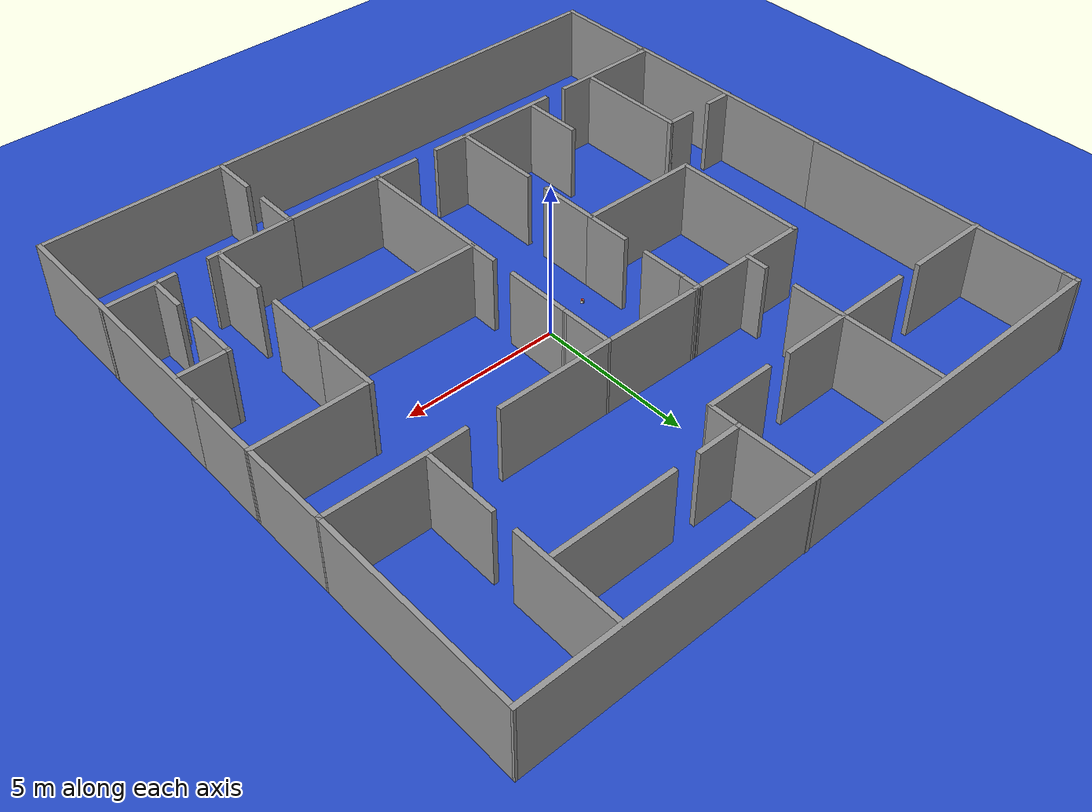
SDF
<sdf version="1.9">
 <world name="diff_drive">
  <physics name="default_physics" default="false" type="ode">
   <max_step_size>0.001</max_step_size>
   <real_time_factor>1</real_time_factor>
   <real_time_update_rate>1000</real_time_update_rate>
  </physics>
  <plugin name="ignition::gazebo::systems::Physics" filename="ignition-gazebo-physics-system"/>
  <plugin name="ignition::gazebo::systems::SceneBroadcaster" filename="ignition-gazebo-scene-broadcaster-system"/>
  <plugin name="gz::sim::systems::Sensors" filename="ignition-gazebo-sensors-system">
   <render_engine>ogre1</render_engine>
  </plugin>
  <gravity>0 0 -9.8</gravity>
  <magnetic_field>6e-06 2.3e-05 -4.2e-05</magnetic_field>
  <atmosphere type="adiabatic"/>
  <scene><ambient>0.4 0.4 0.4 1</ambient><background>0.7 0.7 0.7 1</background><shadows>true</shadows></scene>
  <model name="Untitled">
   <pose>-0.041619 -0.021097 0 0 -0 0</pose>
   <link name="Wall_101">
    <collision name="Wall_101_Collision">
     <geometry><box><size>7.5 0.15 2.5</size></box></geometry>
     <pose>0 0 1.25 0 -0 0</pose>
    </collision>
    <visual name="Wall_101_Visual">
     <pose>0 0 1.25 0 -0 0</pose>
     <geometry><box><size>7.5 0.15 2.5</size></box></geometry>
     <material>
      <script><uri>file://media/materials/scripts/gazebo.material</uri><name>Gazebo/Grey</name></script>
      <ambient>1 1 1 1</ambient>
     </material>
     <meta><layer>0</layer></meta>
    </visual>
    <pose>-9.92842 -2.70817 0 0 -0 1.5708</pose>
   </link>
   <link name="Wall_103">
    <collision name="Wall_103_Collision">
     <geometry><box><size>3.75 0.15 2.5</size></box></geometry>
     <pose>0 0 1.25 0 -0 0</pose>
    </collision>
    <visual name="Wall_103_Visual">
     <pose>0 0 1.25 0 -0 0</pose>
     <geometry><box><size>3.75 0.15 2.5</size></box></geometry>
     <material>
      <script><uri>file://media/materials/scripts/gazebo.material</uri><name>Gazebo/Grey</name></script>
      <ambient>1 1 1 1</ambient>
     </material>
     <meta><layer>0</layer></meta>
    </visual>
    <pose>-7.3963 -4.51708 0 0 -0 1.5708</pose>
   </link>
   <link name="Wall_104">
    <collision name="Wall_104_Collision">
     <geometry><box><size>1 0.15 2.5</size></box></geometry>
     <pose>0 0 1.25 0 -0 0</pose>
    </collision>
    <visual name="Wall_104_Visual">
     <pose>0 0 1.25 0 -0 0</pose>
     <geometry><box><size>1 0.15 2.5</size></box></geometry>
     <material>
      <script><uri>file://media/materials/scripts/gazebo.material</uri><name>Gazebo/Grey</name></script>
      <ambient>1 1 1 1</ambient>
     </material>
     <meta><layer>0</layer></meta>
    </visual>
    <pose>-7.8213 -2.71708 0 0 -0 3.14159</pose>
   </link>
   <link name="Wall_106">
    <collision name="Wall_106_Collision">
     <geometry><box><size>1 0.15 2.5</size></box></geometry>
     <pose>0 0 1.25 0 -0 0</pose>
    </collision>
    <visual name="Wall_106_Visual">
     <pose>0 0 1.25 0 -0 0</pose>
     <geometry><box><size>1 0.15 2.5</size></box></geometry>
     <material>
      <script><uri>file://media/materials/scripts/gazebo.material</uri><name>Gazebo/Grey</name></script>
      <ambient>1 1 1 1</ambient>
     </material>
     <meta><layer>0</layer></meta>
    </visual>
    <pose>-9.5213 -2.71708 0 0 -0 3.14159</pose>
   </link>
   <link name="Wall_110">
    <collision name="Wall_110_Collision">
     <geometry><box><size>8.75 0.15 2.5</size></box></geometry>
     <pose>0 0 1.25 0 -0 0</pose>
    </collision>
    <visual name="Wall_110_Visual">
     <pose>0 0 1.25 0 -0 0</pose>
     <geometry><box><size>8.75 0.15 2.5</size></box></geometry>
     <material>
      <script><uri>file://media/materials/scripts/gazebo.material</uri><name>Gazebo/Grey</name></script>
      <ambient>1 1 1 1</ambient>
     </material>
     <meta><layer>0</layer></meta>
    </visual>
    <pose>-9.92842 5.26683 0 0 -0 1.5708</pose>
   </link>
   <link name="Wall_113">
    <collision name="Wall_113_Collision">
     <geometry><box><size>0.5 0.15 2.5</size></box></geometry>
     <pose>0 0 1.25 0 -0 0</pose>
    </collision>
    <visual name="Wall_113_Visual">
     <pose>0 0 1.25 0 -0 0</pose>
     <geometry><box><size>0.5 0.15 2.5</size></box></geometry>
     <material>
      <script><uri>file://media/materials/scripts/gazebo.material</uri><name>Gazebo/Grey</name></script>
      <ambient>1 1 1 1</ambient>
     </material>
     <meta><layer>0</layer></meta>
    </visual>
    <pose>-9.92842 9.74183 0 0 -0 1.5708</pose>
   </link>
   <link name="Wall_115">
    <collision name="Wall_115_Collision">
     <geometry><box><size>20 0.15 2.5</size></box></geometry>
     <pose>0 0 1.25 0 -0 0</pose>
    </collision>
    <visual name="Wall_115_Visual">
     <pose>0 0 1.25 0 -0 0</pose>
     <geometry><box><size>20 0.15 2.5</size></box></geometry>
     <material>
      <script><uri>file://media/materials/scripts/gazebo.material</uri><name>Gazebo/Grey</name></script>
      <ambient>1 1 1 1</ambient>
     </material>
     <meta><layer>0</layer></meta>
    </visual>
    <pose>-0.003417 9.91683 0 0 -0 0</pose>
   </link>
   <link name="Wall_116">
    <collision name="Wall_116_Collision">
     <geometry><box><size>6.73451 0.15 2.5</size></box></geometry>
     <pose>0 0 1.25 0 -0 0</pose>
    </collision>
    <visual name="Wall_116_Visual">
     <pose>0 0 1.25 0 -0 0</pose>
     <geometry><box><size>6.73451 0.15 2.5</size></box></geometry>
     <material>
      <script><uri>file://media/materials/scripts/gazebo.material</uri><name>Gazebo/Grey</name></script>
      <ambient>1 1 1 1</ambient>
     </material>
     <meta><layer>0</layer></meta>
    </visual>
    <pose>9.92733 6.62458 0 0 -0 -1.56905</pose>
   </link>
   <link name="Wall_120">
    <collision name="Wall_120_Collision">
     <geometry><box><size>3.5 0.15 2.5</size></box></geometry>
     <pose>0 0 1.25 0 -0 0</pose>
    </collision>
    <visual name="Wall_120_Visual">
     <pose>0 0 1.25 0 -0 0</pose>
     <geometry><box><size>3.5 0.15 2.5</size></box></geometry>
     <material>
      <script><uri>file://media/materials/scripts/gazebo.material</uri><name>Gazebo/Grey</name></script>
      <ambient>1 1 1 1</ambient>
     </material>
     <meta><layer>0</layer></meta>
    </visual>
    <pose>6.92773 8.23568 0 0 -0 -1.5708</pose>
   </link>
   <link name="Wall_122">
    <collision name="Wall_122_Collision">
     <geometry><box><size>2.5 0.15 2.5</size></box></geometry>
     <pose>0 0 1.25 0 -0 0</pose>
    </collision>
    <visual name="Wall_122_Visual">
     <pose>0 0 1.25 0 -0 0</pose>
     <geometry><box><size>2.5 0.15 2.5</size></box></geometry>
     <material>
      <script><uri>file://media/materials/scripts/gazebo.material</uri><name>Gazebo/Grey</name></script>
      <ambient>1 1 1 1</ambient>
     </material>
     <meta><layer>0</layer></meta>
    </visual>
    <pose>6.92773 4.53568 0 0 -0 -1.5708</pose>
   </link>
   <link name="Wall_125">
    <collision name="Wall_125_Collision">
     <geometry><box><size>2.75 0.15 2.5</size></box></geometry>
     <pose>0 0 1.25 0 -0 0</pose>
    </collision>
    <visual name="Wall_125_Visual">
     <pose>0 0 1.25 0 -0 0</pose>
     <geometry><box><size>2.75 0.15 2.5</size></box></geometry>
     <material>
      <script><uri>file://media/materials/scripts/gazebo.material</uri><name>Gazebo/Grey</name></script>
      <ambient>1 1 1 1</ambient>
     </material>
     <meta><layer>0</layer></meta>
    </visual>
    <pose>-8.65702 6.67293 0 0 -0 0</pose>
   </link>
   <link name="Wall_127">
    <collision name="Wall_127_Collision">
     <geometry><box><size>2.5 0.15 2.5</size></box></geometry>
     <pose>0 0 1.25 0 -0 0</pose>
    </collision>
    <visual name="Wall_127_Visual">
     <pose>0 0 1.25 0 -0 0</pose>
     <geometry><box><size>2.5 0.15 2.5</size></box></geometry>
     <material>
      <script><uri>file://media/materials/scripts/gazebo.material</uri><name>Gazebo/Grey</name></script>
      <ambient>1 1 1 1</ambient>
     </material>
     <meta><layer>0</layer></meta>
    </visual>
    <pose>-5.33202 6.67293 0 0 -0 0</pose>
   </link>
   <link name="Wall_128">
    <collision name="Wall_128_Collision">
     <geometry><box><size>3.25 0.15 2.5</size></box></geometry>
     <pose>0 0 1.25 0 -0 0</pose>
    </collision>
    <visual name="Wall_128_Visual">
     <pose>0 0 1.25 0 -0 0</pose>
     <geometry><box><size>3.25 0.15 2.5</size></box></geometry>
     <material>
      <script><uri>file://media/materials/scripts/gazebo.material</uri><name>Gazebo/Grey</name></script>
      <ambient>1 1 1 1</ambient>
     </material>
     <meta><layer>0</layer></meta>
    </visual>
    <pose>-4.15702 8.22292 0 0 -0 1.5708</pose>
   </link>
   <link name="Wall_130">
    <collision name="Wall_130_Collision">
     <geometry><box><size>4 0.15 2.5</size></box></geometry>
     <pose>0 0 1.25 0 -0 0</pose>
    </collision>
    <visual name="Wall_130_Visual">
     <pose>0 0 1.25 0 -0 0</pose>
     <geometry><box><size>4 0.15 2.5</size></box></geometry>
     <material>
      <script><uri>file://media/materials/scripts/gazebo.material</uri><name>Gazebo/Grey</name></script>
      <ambient>1 1 1 1</ambient>
     </material>
     <meta><layer>0</layer></meta>
    </visual>
    <pose>4.96545 7.58545 0 0 -0 3.14159</pose>
   </link>
   <link name="Wall_132">
    <collision name="Wall_132_Collision">
     <geometry><box><size>1.46033 0.15 2.5</size></box></geometry>
     <pose>0 0 1.25 0 -0 0</pose>
    </collision>
    <visual name="Wall_132_Visual">
     <pose>0 0 1.25 0 -0 0</pose>
     <geometry><box><size>1.46033 0.15 2.5</size></box></geometry>
     <material>
      <script><uri>file://media/materials/scripts/gazebo.material</uri><name>Gazebo/Grey</name></script>
      <ambient>1 1 1 1</ambient>
     </material>
     <meta><layer>0</layer></meta>
    </visual>
    <pose>1.50869 7.58545 0 0 -0 3.14159</pose>
   </link>
   <link name="Wall_134">
    <collision name="Wall_134_Collision">
     <geometry><box><size>2.50015 0.15 2.5</size></box></geometry>
     <pose>0 0 1.25 0 -0 0</pose>
    </collision>
    <visual name="Wall_134_Visual">
     <pose>0 0 1.25 0 -0 0</pose>
     <geometry><box><size>2.50015 0.15 2.5</size></box></geometry>
     <material>
      <script><uri>file://media/materials/scripts/gazebo.material</uri><name>Gazebo/Grey</name></script>
      <ambient>1 1 1 1</ambient>
     </material>
     <meta><layer>0</layer></meta>
    </visual>
    <pose>0.833691 8.76045 0 0 -0 1.58768</pose>
   </link>
   <link name="Wall_137">
    <collision name="Wall_137_Collision">
     <geometry><box><size>2.25 0.15 2.5</size></box></geometry>
     <pose>0 0 1.25 0 -0 0</pose>
    </collision>
    <visual name="Wall_137_Visual">
     <pose>0 0 1.25 0 -0 0</pose>
     <geometry><box><size>2.25 0.15 2.5</size></box></geometry>
     <material>
      <script><uri>file://media/materials/scripts/gazebo.material</uri><name>Gazebo/Grey</name></script>
      <ambient>1 1 1 1</ambient>
     </material>
     <meta><layer>0</layer></meta>
    </visual>
    <pose>-3.10702 6.67293 0 0 -0 0</pose>
   </link>
   <link name="Wall_139">
    <collision name="Wall_139_Collision">
     <geometry><box><size>2.2 0.15 2.5</size></box></geometry>
     <pose>0 0 1.25 0 -0 0</pose>
    </collision>
    <visual name="Wall_139_Visual">
     <pose>0 0 1.25 0 -0 0</pose>
     <geometry><box><size>2.2 0.15 2.5</size></box></geometry>
     <material>
      <script><uri>file://media/materials/scripts/gazebo.material</uri><name>Gazebo/Grey</name></script>
      <ambient>1 1 1 1</ambient>
     </material>
     <meta><layer>0</layer></meta>
    </visual>
    <pose>-0.182024 6.67293 0 0 -0 0</pose>
   </link>
   <link name="Wall_142">
    <collision name="Wall_142_Collision">
     <geometry><box><size>1 0.15 2.5</size></box></geometry>
     <pose>0 0 1.25 0 -0 0</pose>
    </collision>
    <visual name="Wall_142_Visual">
     <pose>0 0 1.25 0 -0 0</pose>
     <geometry><box><size>1 0.15 2.5</size></box></geometry>
     <material>
      <script><uri>file://media/materials/scripts/gazebo.material</uri><name>Gazebo/Grey</name></script>
      <ambient>1 1 1 1</ambient>
     </material>
     <meta><layer>0</layer></meta>
    </visual>
    <pose>0.853529 7.16045 0 0 -0 -1.5708</pose>
   </link>
   <link name="Wall_144">
    <collision name="Wall_144_Collision">
     <geometry><box><size>1.75 0.15 2.5</size></box></geometry>
     <pose>0 0 1.25 0 -0 0</pose>
    </collision>
    <visual name="Wall_144_Visual">
     <pose>0 0 1.25 0 -0 0</pose>
     <geometry><box><size>1.75 0.15 2.5</size></box></geometry>
     <material>
      <script><uri>file://media/materials/scripts/gazebo.material</uri><name>Gazebo/Grey</name></script>
      <ambient>1 1 1 1</ambient>
     </material>
     <meta><layer>0</layer></meta>
    </visual>
    <pose>-4.15702 5.87292 0 0 -0 -1.5708</pose>
   </link>
   <link name="Wall_146">
    <collision name="Wall_146_Collision">
     <geometry><box><size>0.75 0.15 2.5</size></box></geometry>
     <pose>0 0 1.25 0 -0 0</pose>
    </collision>
    <visual name="Wall_146_Visual">
     <pose>0 0 1.25 0 -0 0</pose>
     <geometry><box><size>0.75 0.15 2.5</size></box></geometry>
     <material>
      <script><uri>file://media/materials/scripts/gazebo.material</uri><name>Gazebo/Grey</name></script>
      <ambient>1 1 1 1</ambient>
     </material>
     <meta><layer>0</layer></meta>
    </visual>
    <pose>-4.15702 3.67292 0 0 -0 -1.5708</pose>
   </link>
   <link name="Wall_148">
    <collision name="Wall_148_Collision">
     <geometry><box><size>3.75 0.15 2.5</size></box></geometry>
     <pose>0 0 1.25 0 -0 0</pose>
    </collision>
    <visual name="Wall_148_Visual">
     <pose>0 0 1.25 0 -0 0</pose>
     <geometry><box><size>3.75 0.15 2.5</size></box></geometry>
     <material>
      <script><uri>file://media/materials/scripts/gazebo.material</uri><name>Gazebo/Grey</name></script>
      <ambient>1 1 1 1</ambient>
     </material>
     <meta><layer>0</layer></meta>
    </visual>
    <pose>2.84858 3.34383 0 0 -0 0</pose>
   </link>
   <link name="Wall_150">
    <collision name="Wall_150_Collision">
     <geometry><box><size>1.32927 0.15 2.5</size></box></geometry>
     <pose>0 0 1.25 0 -0 0</pose>
    </collision>
    <visual name="Wall_150_Visual">
     <pose>0 0 1.25 0 -0 0</pose>
     <geometry><box><size>1.32927 0.15 2.5</size></box></geometry>
     <material>
      <script><uri>file://media/materials/scripts/gazebo.material</uri><name>Gazebo/Grey</name></script>
      <ambient>1 1 1 1</ambient>
     </material>
     <meta><layer>0</layer></meta>
    </visual>
    <pose>6.33816 3.35225 0 0 -0 0.014288</pose>
   </link>
   <link name="Wall_151">
    <collision name="Wall_151_Collision">
     <geometry><box><size>3.15549 0.15 2.5</size></box></geometry>
     <pose>0 0 1.25 0 -0 0</pose>
    </collision>
    <visual name="Wall_151_Visual">
     <pose>0 0 1.25 0 -0 0</pose>
     <geometry><box><size>3.15549 0.15 2.5</size></box></geometry>
     <material>
      <script><uri>file://media/materials/scripts/gazebo.material</uri><name>Gazebo/Grey</name></script>
      <ambient>1 1 1 1</ambient>
     </material>
     <meta><layer>0</layer></meta>
    </visual>
    <pose>8.43041 3.3465 0 0 -0 -0.009432</pose>
   </link>
   <link name="Wall_25">
    <collision name="Wall_25_Collision">
     <geometry><box><size>20 0.15 2.5</size></box></geometry>
     <pose>0 0 1.25 0 -0 0</pose>
    </collision>
    <visual name="Wall_25_Visual">
     <pose>0 0 1.25 0 -0 0</pose>
     <geometry><box><size>20 0.15 2.5</size></box></geometry>
     <material>
      <script><uri>file://media/materials/scripts/gazebo.material</uri><name>Gazebo/Grey</name></script>
      <ambient>1 1 1 1</ambient>
     </material>
     <meta><layer>0</layer></meta>
    </visual>
    <pose>0.020014 -9.93661 0 0 -0 0</pose>
   </link>
   <link name="Wall_27">
    <collision name="Wall_27_Collision">
     <geometry><box><size>8.25 0.15 2.5</size></box></geometry>
     <pose>0 0 1.25 0 -0 0</pose>
    </collision>
    <visual name="Wall_27_Visual">
     <pose>0 0 1.25 0 -0 0</pose>
     <geometry><box><size>8.25 0.15 2.5</size></box></geometry>
     <material>
      <script><uri>file://media/materials/scripts/gazebo.material</uri><name>Gazebo/Grey</name></script>
      <ambient>1 1 1 1</ambient>
     </material>
     <meta><layer>0</layer></meta>
    </visual>
    <pose>9.94501 -5.88661 0 0 -0 1.5708</pose>
   </link>
   <link name="Wall_29">
    <collision name="Wall_29_Collision">
     <geometry><box><size>1.5 0.15 2.5</size></box></geometry>
     <pose>0 0 1.25 0 -0 0</pose>
    </collision>
    <visual name="Wall_29_Visual">
     <pose>0 0 1.25 0 -0 0</pose>
     <geometry><box><size>1.5 0.15 2.5</size></box></geometry>
     <material>
      <script><uri>file://media/materials/scripts/gazebo.material</uri><name>Gazebo/Grey</name></script>
      <ambient>1 1 1 1</ambient>
     </material>
     <meta><layer>0</layer></meta>
    </visual>
    <pose>4.15702 -9.26161 0 0 -0 1.5708</pose>
   </link>
   <link name="Wall_31">
    <collision name="Wall_31_Collision">
     <geometry><box><size>1.49705 0.15 2.5</size></box></geometry>
     <pose>0 0 1.25 0 -0 0</pose>
    </collision>
    <visual name="Wall_31_Visual">
     <pose>0 0 1.25 0 -0 0</pose>
     <geometry><box><size>1.49705 0.15 2.5</size></box></geometry>
     <material>
      <script><uri>file://media/materials/scripts/gazebo.material</uri><name>Gazebo/Grey</name></script>
      <ambient>1 1 1 1</ambient>
     </material>
     <meta><layer>0</layer></meta>
    </visual>
    <pose>4.1585 -7.06309 0 0 -0 1.5686</pose>
   </link>
   <link name="Wall_33">
    <collision name="Wall_33_Collision">
     <geometry><box><size>2.75 0.15 2.5</size></box></geometry>
     <pose>0 0 1.25 0 -0 0</pose>
    </collision>
    <visual name="Wall_33_Visual">
     <pose>0 0 1.25 0 -0 0</pose>
     <geometry><box><size>2.75 0.15 2.5</size></box></geometry>
     <material>
      <script><uri>file://media/materials/scripts/gazebo.material</uri><name>Gazebo/Grey</name></script>
      <ambient>1 1 1 1</ambient>
     </material>
     <meta><layer>0</layer></meta>
    </visual>
    <pose>5.45129 -6.38087 0 0 -0 0</pose>
   </link>
   <link name="Wall_35">
    <collision name="Wall_35_Collision">
     <geometry><box><size>2.25 0.15 2.5</size></box></geometry>
     <pose>0 0 1.25 0 -0 0</pose>
    </collision>
    <visual name="Wall_35_Visual">
     <pose>0 0 1.25 0 -0 0</pose>
     <geometry><box><size>2.25 0.15 2.5</size></box></geometry>
     <material>
      <script><uri>file://media/materials/scripts/gazebo.material</uri><name>Gazebo/Grey</name></script>
      <ambient>1 1 1 1</ambient>
     </material>
     <meta><layer>0</layer></meta>
    </visual>
    <pose>8.90702 -6.38661 0 0 -0 0</pose>
   </link>
   <link name="Wall_37">
    <collision name="Wall_37_Collision">
     <geometry><box><size>1.25 0.15 2.5</size></box></geometry>
     <pose>0 0 1.25 0 -0 0</pose>
    </collision>
    <visual name="Wall_37_Visual">
     <pose>0 0 1.25 0 -0 0</pose>
     <geometry><box><size>1.25 0.15 2.5</size></box></geometry>
     <material>
      <script><uri>file://media/materials/scripts/gazebo.material</uri><name>Gazebo/Grey</name></script>
      <ambient>1 1 1 1</ambient>
     </material>
     <meta><layer>0</layer></meta>
    </visual>
    <pose>8.41023 -5.80349 0 0 -0 1.5708</pose>
   </link>
   <link name="Wall_39">
    <collision name="Wall_39_Collision">
     <geometry><box><size>1.75 0.15 2.5</size></box></geometry>
     <pose>0 0 1.25 0 -0 0</pose>
    </collision>
    <visual name="Wall_39_Visual">
     <pose>0 0 1.25 0 -0 0</pose>
     <geometry><box><size>1.75 0.15 2.5</size></box></geometry>
     <material>
      <script><uri>file://media/materials/scripts/gazebo.material</uri><name>Gazebo/Grey</name></script>
      <ambient>1 1 1 1</ambient>
     </material>
     <meta><layer>0</layer></meta>
    </visual>
    <pose>8.41023 -3.60349 0 0 -0 1.5708</pose>
   </link>
   <link name="Wall_40">
    <collision name="Wall_40_Collision">
     <geometry><box><size>1.6 0.15 2.5</size></box></geometry>
     <pose>0 0 1.25 0 -0 0</pose>
    </collision>
    <visual name="Wall_40_Visual">
     <pose>0 0 1.25 0 -0 0</pose>
     <geometry><box><size>1.6 0.15 2.5</size></box></geometry>
     <material>
      <script><uri>file://media/materials/scripts/gazebo.material</uri><name>Gazebo/Grey</name></script>
      <ambient>1 1 1 1</ambient>
     </material>
     <meta><layer>0</layer></meta>
    </visual>
    <pose>9.13523 -2.80349 0 0 -0 0</pose>
   </link>
   <link name="Wall_42">
    <collision name="Wall_42_Collision">
     <geometry><box><size>2 0.15 2.5</size></box></geometry>
     <pose>0 0 1.25 0 -0 0</pose>
    </collision>
    <visual name="Wall_42_Visual">
     <pose>0 0 1.25 0 -0 0</pose>
     <geometry><box><size>2 0.15 2.5</size></box></geometry>
     <material>
      <script><uri>file://media/materials/scripts/gazebo.material</uri><name>Gazebo/Grey</name></script>
      <ambient>1 1 1 1</ambient>
     </material>
     <meta><layer>0</layer></meta>
    </visual>
    <pose>6.46332 -5.39614 0 0 -0 1.5708</pose>
   </link>
   <link name="Wall_44">
    <collision name="Wall_44_Collision">
     <geometry><box><size>2.25 0.15 2.5</size></box></geometry>
     <pose>0 0 1.25 0 -0 0</pose>
    </collision>
    <visual name="Wall_44_Visual">
     <pose>0 0 1.25 0 -0 0</pose>
     <geometry><box><size>2.25 0.15 2.5</size></box></geometry>
     <material>
      <script><uri>file://media/materials/scripts/gazebo.material</uri><name>Gazebo/Grey</name></script>
      <ambient>1 1 1 1</ambient>
     </material>
     <meta><layer>0</layer></meta>
    </visual>
    <pose>6.46332 -2.57114 0 0 -0 1.5708</pose>
   </link>
   <link name="Wall_50">
    <collision name="Wall_50_Collision">
     <geometry><box><size>5.5 0.15 2.5</size></box></geometry>
     <pose>0 0 1.25 0 -0 0</pose>
    </collision>
    <visual name="Wall_50_Visual">
     <pose>0 0 1.25 0 -0 0</pose>
     <geometry><box><size>5.5 0.15 2.5</size></box></geometry>
     <material>
      <script><uri>file://media/materials/scripts/gazebo.material</uri><name>Gazebo/Grey</name></script>
      <ambient>1 1 1 1</ambient>
     </material>
     <meta><layer>0</layer></meta>
    </visual>
    <pose>3.74658 -2.03317 0 0 -0 3.14159</pose>
   </link>
   <link name="Wall_51">
    <collision name="Wall_51_Collision">
     <geometry><box><size>4.5 0.15 2.5</size></box></geometry>
     <pose>0 0 1.25 0 -0 0</pose>
    </collision>
    <visual name="Wall_51_Visual">
     <pose>0 0 1.25 0 -0 0</pose>
     <geometry><box><size>4.5 0.15 2.5</size></box></geometry>
     <material>
      <script><uri>file://media/materials/scripts/gazebo.material</uri><name>Gazebo/Grey</name></script>
      <ambient>1 1 1 1</ambient>
     </material>
     <meta><layer>0</layer></meta>
    </visual>
    <pose>1.07158 -4.20817 0 0 -0 -1.5708</pose>
   </link>
   <link name="Wall_52">
    <collision name="Wall_52_Collision">
     <geometry><box><size>3.23841 0.15 2.5</size></box></geometry>
     <pose>0 0 1.25 0 -0 0</pose>
    </collision>
    <visual name="Wall_52_Visual">
     <pose>0 0 1.25 0 -0 0</pose>
     <geometry><box><size>3.23841 0.15 2.5</size></box></geometry>
     <material>
      <script><uri>file://media/materials/scripts/gazebo.material</uri><name>Gazebo/Grey</name></script>
      <ambient>1 1 1 1</ambient>
     </material>
     <meta><layer>0</layer></meta>
    </visual>
    <pose>2.61578 -6.38637 0 0 -0 -0.002071</pose>
   </link>
   <link name="Wall_54">
    <collision name="Wall_54_Collision">
     <geometry><box><size>2.5 0.15 2.5</size></box></geometry>
     <pose>0 0 1.25 0 -0 0</pose>
    </collision>
    <visual name="Wall_54_Visual">
     <pose>0 0 1.25 0 -0 0</pose>
     <geometry><box><size>2.5 0.15 2.5</size></box></geometry>
     <material>
      <script><uri>file://media/materials/scripts/gazebo.material</uri><name>Gazebo/Grey</name></script>
      <ambient>1 1 1 1</ambient>
     </material>
     <meta><layer>0</layer></meta>
    </visual>
    <pose>9.94501 -0.661611 0 0 -0 1.5708</pose>
   </link>
   <link name="Wall_55">
    <collision name="Wall_55_Collision">
     <geometry><box><size>3.5 0.15 2.5</size></box></geometry>
     <pose>0 0 1.25 0 -0 0</pose>
    </collision>
    <visual name="Wall_55_Visual">
     <pose>0 0 1.25 0 -0 0</pose>
     <geometry><box><size>3.5 0.15 2.5</size></box></geometry>
     <material>
      <script><uri>file://media/materials/scripts/gazebo.material</uri><name>Gazebo/Grey</name></script>
      <ambient>1 1 1 1</ambient>
     </material>
     <meta><layer>0</layer></meta>
    </visual>
    <pose>8.27001 0.513389 0 0 -0 3.14159</pose>
   </link>
   <link name="Wall_58">
    <collision name="Wall_58_Collision">
     <geometry><box><size>2.2 0.15 2.5</size></box></geometry>
     <pose>0 0 1.25 0 -0 0</pose>
    </collision>
    <visual name="Wall_58_Visual">
     <pose>0 0 1.25 0 -0 0</pose>
     <geometry><box><size>2.2 0.15 2.5</size></box></geometry>
     <material>
      <script><uri>file://media/materials/scripts/gazebo.material</uri><name>Gazebo/Grey</name></script>
      <ambient>1 1 1 1</ambient>
     </material>
     <meta><layer>0</layer></meta>
    </visual>
    <pose>6.46332 -0.496143 0 0 -0 1.5708</pose>
   </link>
   <link name="Wall_60">
    <collision name="Wall_60_Collision">
     <geometry><box><size>1.5 0.15 2.5</size></box></geometry>
     <pose>0 0 1.25 0 -0 0</pose>
    </collision>
    <visual name="Wall_60_Visual">
     <pose>0 0 1.25 0 -0 0</pose>
     <geometry><box><size>1.5 0.15 2.5</size></box></geometry>
     <material>
      <script><uri>file://media/materials/scripts/gazebo.material</uri><name>Gazebo/Grey</name></script>
      <ambient>1 1 1 1</ambient>
     </material>
     <meta><layer>0</layer></meta>
    </visual>
    <pose>0.396583 -6.38317 0 0 -0 3.14159</pose>
   </link>
   <link name="Wall_62">
    <collision name="Wall_62_Collision">
     <geometry><box><size>4.5 0.15 2.5</size></box></geometry>
     <pose>0 0 1.25 0 -0 0</pose>
    </collision>
    <visual name="Wall_62_Visual">
     <pose>0 0 1.25 0 -0 0</pose>
     <geometry><box><size>4.5 0.15 2.5</size></box></geometry>
     <material>
      <script><uri>file://media/materials/scripts/gazebo.material</uri><name>Gazebo/Grey</name></script>
      <ambient>1 1 1 1</ambient>
     </material>
     <meta><layer>0</layer></meta>
    </visual>
    <pose>-3.30342 -6.38317 0 0 -0 3.14159</pose>
   </link>
   <link name="Wall_64">
    <collision name="Wall_64_Collision">
     <geometry><box><size>1 0.15 2.5</size></box></geometry>
     <pose>0 0 1.25 0 -0 0</pose>
    </collision>
    <visual name="Wall_64_Visual">
     <pose>0 0 1.25 0 -0 0</pose>
     <geometry><box><size>1 0.15 2.5</size></box></geometry>
     <material>
      <script><uri>file://media/materials/scripts/gazebo.material</uri><name>Gazebo/Grey</name></script>
      <ambient>1 1 1 1</ambient>
     </material>
     <meta><layer>0</layer></meta>
    </visual>
    <pose>1.07158 -1.60817 0 0 -0 1.5708</pose>
   </link>
   <link name="Wall_67">
    <collision name="Wall_67_Collision">
     <geometry><box><size>2.25 0.15 2.5</size></box></geometry>
     <pose>0 0 1.25 0 -0 0</pose>
    </collision>
    <visual name="Wall_67_Visual">
     <pose>0 0 1.25 0 -0 0</pose>
     <geometry><box><size>2.25 0.15 2.5</size></box></geometry>
     <material>
      <script><uri>file://media/materials/scripts/gazebo.material</uri><name>Gazebo/Grey</name></script>
      <ambient>1 1 1 1</ambient>
     </material>
     <meta><layer>0</layer></meta>
    </visual>
    <pose>1.07158 0.716827 0 0 -0 1.5708</pose>
   </link>
   <link name="Wall_68">
    <collision name="Wall_68_Collision">
     <geometry><box><size>1.72717 0.15 2.5</size></box></geometry>
     <pose>0 0 1.25 0 -0 0</pose>
    </collision>
    <visual name="Wall_68_Visual">
     <pose>0 0 1.25 0 -0 0</pose>
     <geometry><box><size>1.72717 0.15 2.5</size></box></geometry>
     <material>
      <script><uri>file://media/materials/scripts/gazebo.material</uri><name>Gazebo/Grey</name></script>
      <ambient>1 1 1 1</ambient>
     </material>
     <meta><layer>0</layer></meta>
    </visual>
    <pose>1.06583 2.55533 0 0 -0 1.57809</pose>
   </link>
   <link name="Wall_70">
    <collision name="Wall_70_Collision">
     <geometry><box><size>2.96904 0.15 2.5</size></box></geometry>
     <pose>0 0 1.25 0 -0 0</pose>
    </collision>
    <visual name="Wall_70_Visual">
     <pose>0 0 1.25 0 -0 0</pose>
     <geometry><box><size>2.96904 0.15 2.5</size></box></geometry>
     <material>
      <script><uri>file://media/materials/scripts/gazebo.material</uri><name>Gazebo/Grey</name></script>
      <ambient>1 1 1 1</ambient>
     </material>
     <meta><layer>0</layer></meta>
    </visual>
    <pose>9.93905 1.92286 0 0 -0 -1.56656</pose>
   </link>
   <link name="Wall_72">
    <collision name="Wall_72_Collision">
     <geometry><box><size>3 0.15 2.5</size></box></geometry>
     <pose>0 0 1.25 0 -0 0</pose>
    </collision>
    <visual name="Wall_72_Visual">
     <pose>0 0 1.25 0 -0 0</pose>
     <geometry><box><size>3 0.15 2.5</size></box></geometry>
     <material>
      <script><uri>file://media/materials/scripts/gazebo.material</uri><name>Gazebo/Grey</name></script>
      <ambient>1 1 1 1</ambient>
     </material>
     <meta><layer>0</layer></meta>
    </visual>
    <pose>-2.23287 -4.9408 0 0 -0 1.5708</pose>
   </link>
   <link name="Wall_76">
    <collision name="Wall_76_Collision">
     <geometry><box><size>2 0.15 2.5</size></box></geometry>
     <pose>0 0 1.25 0 -0 0</pose>
    </collision>
    <visual name="Wall_76_Visual">
     <pose>0 0 1.25 0 -0 0</pose>
     <geometry><box><size>2 0.15 2.5</size></box></geometry>
     <material>
      <script><uri>file://media/materials/scripts/gazebo.material</uri><name>Gazebo/Grey</name></script>
      <ambient>1 1 1 1</ambient>
     </material>
     <meta><layer>0</layer></meta>
    </visual>
    <pose>-2.23287 -1.7408 0 0 -0 1.5708</pose>
   </link>
   <link name="Wall_77">
    <collision name="Wall_77_Collision">
     <geometry><box><size>4 0.15 2.5</size></box></geometry>
     <pose>0 0 1.25 0 -0 0</pose>
    </collision>
    <visual name="Wall_77_Visual">
     <pose>0 0 1.25 0 -0 0</pose>
     <geometry><box><size>4 0.15 2.5</size></box></geometry>
     <material>
      <script><uri>file://media/materials/scripts/gazebo.material</uri><name>Gazebo/Grey</name></script>
      <ambient>1 1 1 1</ambient>
     </material>
     <meta><layer>0</layer></meta>
    </visual>
    <pose>-4.15787 -0.815797 0 0 -0 3.14159</pose>
   </link>
   <link name="Wall_79">
    <collision name="Wall_79_Collision">
     <geometry><box><size>1.5 0.15 2.5</size></box></geometry>
     <pose>0 0 1.25 0 -0 0</pose>
    </collision>
    <visual name="Wall_79_Visual">
     <pose>0 0 1.25 0 -0 0</pose>
     <geometry><box><size>1.5 0.15 2.5</size></box></geometry>
     <material>
      <script><uri>file://media/materials/scripts/gazebo.material</uri><name>Gazebo/Grey</name></script>
      <ambient>1 1 1 1</ambient>
     </material>
     <meta><layer>0</layer></meta>
    </visual>
    <pose>-2.23287 -0.140797 0 0 -0 1.5708</pose>
   </link>
   <link name="Wall_81">
    <collision name="Wall_81_Collision">
     <geometry><box><size>1.5 0.15 2.5</size></box></geometry>
     <pose>0 0 1.25 0 -0 0</pose>
    </collision>
    <visual name="Wall_81_Visual">
     <pose>0 0 1.25 0 -0 0</pose>
     <geometry><box><size>1.5 0.15 2.5</size></box></geometry>
     <material>
      <script><uri>file://media/materials/scripts/gazebo.material</uri><name>Gazebo/Grey</name></script>
      <ambient>1 1 1 1</ambient>
     </material>
     <meta><layer>0</layer></meta>
    </visual>
    <pose>-2.23287 2.0592 0 0 -0 1.5708</pose>
   </link>
   <link name="Wall_85">
    <collision name="Wall_85_Collision">
     <geometry><box><size>3.31908 0.15 2.5</size></box></geometry>
     <pose>0 0 1.25 0 -0 0</pose>
    </collision>
    <visual name="Wall_85_Visual">
     <pose>0 0 1.25 0 -0 0</pose>
     <geometry><box><size>3.31908 0.15 2.5</size></box></geometry>
     <material>
      <script><uri>file://media/materials/scripts/gazebo.material</uri><name>Gazebo/Grey</name></script>
      <ambient>1 1 1 1</ambient>
     </material>
     <meta><layer>0</layer></meta>
    </visual>
    <pose>-0.535917 3.35533 0 0 -0 3.13434</pose>
   </link>
   <link name="Wall_86">
    <collision name="Wall_86_Collision">
     <geometry><box><size>0.25 0.15 2.5</size></box></geometry>
     <pose>0 0 1.25 0 -0 0</pose>
    </collision>
    <visual name="Wall_86_Visual">
     <pose>0 0 1.25 0 -0 0</pose>
     <geometry><box><size>0.25 0.15 2.5</size></box></geometry>
     <material>
      <script><uri>file://media/materials/scripts/gazebo.material</uri><name>Gazebo/Grey</name></script>
      <ambient>1 1 1 1</ambient>
     </material>
     <meta><layer>0</layer></meta>
    </visual>
    <pose>-2.15892 3.36683 0 0 -0 3.14159</pose>
   </link>
   <link name="Wall_88">
    <collision name="Wall_88_Collision">
     <geometry><box><size>0.782747 0.15 2.5</size></box></geometry>
     <pose>0 0 1.25 0 -0 0</pose>
    </collision>
    <visual name="Wall_88_Visual">
     <pose>0 0 1.25 0 -0 0</pose>
     <geometry><box><size>0.782747 0.15 2.5</size></box></geometry>
     <material>
      <script><uri>file://media/materials/scripts/gazebo.material</uri><name>Gazebo/Grey</name></script>
      <ambient>1 1 1 1</ambient>
     </material>
     <meta><layer>0</layer></meta>
    </visual>
    <pose>-2.22664 3.05051 0 0 -0 1.55111</pose>
   </link>
   <link name="Wall_90">
    <collision name="Wall_90_Collision">
     <geometry><box><size>4 0.15 2.5</size></box></geometry>
     <pose>0 0 1.25 0 -0 0</pose>
    </collision>
    <visual name="Wall_90_Visual">
     <pose>0 0 1.25 0 -0 0</pose>
     <geometry><box><size>4 0.15 2.5</size></box></geometry>
     <material>
      <script><uri>file://media/materials/scripts/gazebo.material</uri><name>Gazebo/Grey</name></script>
      <ambient>1 1 1 1</ambient>
     </material>
     <meta><layer>0</layer></meta>
    </visual>
    <pose>-4.14542 3.36683 0 0 -0 3.14159</pose>
   </link>
   <link name="Wall_91">
    <collision name="Wall_91_Collision">
     <geometry><box><size>4.25 0.15 2.5</size></box></geometry>
     <pose>0 0 1.25 0 -0 0</pose>
    </collision>
    <visual name="Wall_91_Visual">
     <pose>0 0 1.25 0 -0 0</pose>
     <geometry><box><size>4.25 0.15 2.5</size></box></geometry>
     <material>
      <script><uri>file://media/materials/scripts/gazebo.material</uri><name>Gazebo/Grey</name></script>
      <ambient>1 1 1 1</ambient>
     </material>
     <meta><layer>0</layer></meta>
    </visual>
    <pose>-6.07042 1.31683 0 0 -0 -1.5708</pose>
   </link>
   <link name="Wall_93">
    <collision name="Wall_93_Collision">
     <geometry><box><size>3.5 0.15 2.5</size></box></geometry>
     <pose>0 0 1.25 0 -0 0</pose>
    </collision>
    <visual name="Wall_93_Visual">
     <pose>0 0 1.25 0 -0 0</pose>
     <geometry><box><size>3.5 0.15 2.5</size></box></geometry>
     <material>
      <script><uri>file://media/materials/scripts/gazebo.material</uri><name>Gazebo/Grey</name></script>
      <ambient>1 1 1 1</ambient>
     </material>
     <meta><layer>0</layer></meta>
    </visual>
    <pose>-9.90499 -8.26161 0 0 -0 1.5708</pose>
   </link>
   <link name="Wall_96">
    <collision name="Wall_96_Collision">
     <geometry><box><size>3.75 0.15 2.5</size></box></geometry>
     <pose>0 0 1.25 0 -0 0</pose>
    </collision>
    <visual name="Wall_96_Visual">
     <pose>0 0 1.25 0 -0 0</pose>
     <geometry><box><size>3.75 0.15 2.5</size></box></geometry>
     <material>
      <script><uri>file://media/materials/scripts/gazebo.material</uri><name>Gazebo/Grey</name></script>
      <ambient>1 1 1 1</ambient>
     </material>
     <meta><layer>0</layer></meta>
    </visual>
    <pose>-8.12842 -6.38317 0 0 -0 3.14159</pose>
   </link>
   <link name="Wall_97">
    <collision name="Wall_97_Collision">
     <geometry><box><size>0.354783 0.15 2.5</size></box></geometry>
     <pose>0 0 1.25 0 -0 0</pose>
    </collision>
    <visual name="Wall_97_Visual">
     <pose>0 0 1.25 0 -0 0</pose>
     <geometry><box><size>0.354783 0.15 2.5</size></box></geometry>
     <material>
      <script><uri>file://media/materials/scripts/gazebo.material</uri><name>Gazebo/Grey</name></script>
      <ambient>1 1 1 1</ambient>
     </material>
     <meta><layer>0</layer></meta>
    </visual>
    <pose>-9.9167 -6.48489 0 0 -0 -1.45612</pose>
   </link>
   <link name="Wall_99">
    <collision name="Wall_99_Collision">
     <geometry><box><size>2 0.15 2.5</size></box></geometry>
     <pose>0 0 1.25 0 -0 0</pose>
    </collision>
    <visual name="Wall_99_Visual">
     <pose>0 0 1.25 0 -0 0</pose>
     <geometry><box><size>2 0.15 2.5</size></box></geometry>
     <material>
      <script><uri>file://media/materials/scripts/gazebo.material</uri><name>Gazebo/Grey</name></script>
      <ambient>1 1 1 1</ambient>
     </material>
     <meta><layer>0</layer></meta>
    </visual>
    <pose>-4.87751 -5.40927 0 0 -0 1.5708</pose>
   </link>
   <static>1</static>
  </model>
  <model name="ground_plane">
   <static>true</static>
   <link name="link">
    <collision name="collision">
     <geometry><plane><normal>0 0 1</normal><size>100 100</size></plane></geometry>
     <surface><friction><ode><mu>100</mu><mu2>50</mu2></ode></friction></surface>
    </collision>
    <visual name="visual">
     <cast_shadows>false</cast_shadows>
     <geometry><plane><normal>0 0 1</normal><size>100 100</size></plane></geometry>
     <material>
      <script><uri>file://media/materials/scripts/gazebo.material</uri><name>Gazebo/Blue</name></script>
      <shader type="pixel"><normal_map>__default__</normal_map></shader>
      <ambient>1 1 1 1</ambient>
      <diffuse>1 1 1 1</diffuse>
      <specular>0 0 0 1</specular>
      <emissive>0 0 0 1</emissive>
     </material>
    </visual>
    <inertial>
     <mass>1</mass>
     <inertia><ixx>1</ixx><ixy>0</ixy><ixz>0</ixz><iyy>1</iyy><iyz>0</iyz><izz>1</izz></inertia>
    </inertial>
   </link>
  </model>
  <include>
   <uri>file://src/robot_sim/gazebo/kris_robot</uri>
   <name>kris_robot</name>
   <pose>0 0 0.5 0 -0 3.14</pose>
  </include>
  <include>
   <uri>file://src/robot_sim/gazebo/kris_robot1</uri>
   <name>kris_robot1</name>
   <pose>-1.2 0 0.5 0 -0 3.14</pose>
  </include>
  <light name="sun" type="directional">
   <pose>0 0 10 0 -0 0</pose>
   <intensity>1</intensity>
   <direction>-0.5 0.1 -0.9</direction>
   <diffuse>0.8 0.8 0.8 1</diffuse>
   <specular>0.2 0.2 0.2 1</specular>
   <attenuation>
    <range>1000</range>
    <linear>0.01</linear>
    <constant>0.90000000000000002</constant>
    <quadratic>0.001</quadratic>
   </attenuation>
   <spot><inner_angle>0</inner_angle><outer_angle>0</outer_angle><falloff>0</falloff></spot>
  </light>
 </world>
</sdf>

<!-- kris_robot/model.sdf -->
<sdf version='1.7'>
  <model name='kris_robot1'>
    <link name='kris_robot1_base_link'>
      <pose>0 0 0 0 0 0</pose>
      <inertial>
        <mass>0.25</mass>
        <inertia>
          <ixx>0.0003223</ixx>
          <ixy>0</ixy>
          <ixz>0</ixz>
          <iyy>0.0003223</iyy>
          <iyz>0</iyz>
          <izz>0.0003781</izz>
        </inertia>
        <pose>0 0 0 0 0 0</pose>
        <origin xyz='0 0 0' rpy='0 0 0'/>
      </inertial>
      <self_collide>0</self_collide>
      <enable_wind>0</enable_wind>
      <kinematic>0</kinematic>
      <gravity>1</gravity>
      <visual name='visual'>
        <geometry>
          <cylinder>
            <length>0.08</length>
            <radius>0.055</radius>
          </cylinder>
        </geometry>
        <material>
          <script>
            <uri>file://media/materials/scripts/gazebo.material</uri>
            <name>Gazebo/White</name>
          </script>
          <shader type='pixel'>
            <normal_map>__default__</normal_map>
          </shader>
          <ambient>1 1 1 1</ambient>
          <diffuse>1 1 1 1</diffuse>
          <specular>0 0 0 1</specular>
          <emissive>0 0 0 1</emissive>
        </material>
        <pose>0 0 0.008 0 0 0</pose>
        <transparency>0</transparency>
        <cast_shadows>1</cast_shadows>
        <origin rpy='0 0 0' xyz='0 0 0'/>
      </visual>
      <collision name='collision'>
        <laser_retro>0</laser_retro>
        <max_contacts>10</max_contacts>
        <pose>0 0 0.008 0 0 0</pose>
        <geometry>
          <cylinder>
            <radius>0.055</radius>
            <length>0.08</length>
          </cylinder>
        </geometry>
        <surface>
          <friction>
            <ode>
              <mu>1</mu>
              <mu2>1</mu2>
              <fdir1>0 0 0</fdir1>
              <slip1>0</slip1>
              <slip2>0</slip2>
            </ode>
            <torsional>
              <coefficient>1</coefficient>
              <patch_radius>0</patch_radius>
              <surface_radius>0</surface_radius>
              <use_patch_radius>1</use_patch_radius>
              <ode>
                <slip>0</slip>
              </ode>
            </torsional>
          </friction>
          <bounce>
            <restitution_coefficient>0</restitution_coefficient>
            <threshold>1e+06</threshold>
          </bounce>
          <contact>
            <collide_without_contact>0</collide_without_contact>
            <collide_without_contact_bitmask>1</collide_without_contact_bitmask>
            <collide_bitmask>1</collide_bitmask>
            <ode>
              <soft_cfm>0</soft_cfm>
              <soft_erp>0.2</soft_erp>
              <kp>1e+13</kp>
              <kd>1</kd>
              <max_vel>0.01</max_vel>
              <min_depth>0</min_depth>
            </ode>
            <bullet>
              <split_impulse>1</split_impulse>
              <split_impulse_penetration_threshold>-0.01</split_impulse_penetration_threshold>
              <soft_cfm>0</soft_cfm>
              <soft_erp>0.2</soft_erp>
              <kp>1e+13</kp>
              <kd>1</kd>
            </bullet>
          </contact>
        </surface>
      </collision>
    </link>
    <link name='lidar_link'>
      <inertial>
        <mass>0.047</mass>
        <inertia>
          <ixx>2.716e-05</ixx>
          <ixy>0</ixy>
          <ixz>0</ixz>
          <iyy>1.363e-05</iyy>
          <iyz>0</iyz>
          <izz>1.363e-05</izz>
        </inertia>
        <pose>0 0 0.1 0 0 0</pose>
        <origin xyz='0 0 0' rpy='0 0 0'/>
      </inertial>
      <self_collide>0</self_collide>
      <enable_wind>0</enable_wind>
      <kinematic>0</kinematic>
      <pose>0 0 0 0 0 0</pose>
      <gravity>1</gravity>
      <visual name='visual'>
        <geometry>
          <cylinder>
            <length>0.03</length>
            <radius>0.034</radius>
          </cylinder>
        </geometry>
        <material>
          <script>
            <uri>file://media/materials/scripts/gazebo.material</uri>
            <name>Gazebo/Red</name>
          </script>
          <shader type='pixel'>
            <normal_map>__default__</normal_map>
          </shader>
          <ambient>1 0 0 1</ambient>
          <diffuse>1 0 0 1</diffuse>
          <specular>0.1 0.1 0.1 1</specular>
          <emissive>0 0 0 1</emissive>
        </material>
        <pose>0 0 0.055 0 0 0</pose>
        <transparency>0</transparency>
        <cast_shadows>1</cast_shadows>
        <origin xyz='0 0 0' rpy='0 0 0'/>
      </visual>
      <sensor name='gpu_lidar' type='gpu_lidar'>
        <pose>0 0 0.055 0 0 0</pose>
        <topic>/kris_robot1/scan</topic>
        <gz_frame_id>kris_robot1_base_link</gz_frame_id>
        <update_rate>5</update_rate>
        <enable_metrics>false</enable_metrics>
        <lidar>
          <scan>
            <horizontal>
              <samples>450</samples>
              <resolution>1</resolution>
              <min_angle>0</min_angle>
              <max_angle>6.28</max_angle>
            </horizontal>
            <vertical>
              <samples>1</samples>
              <min_angle>0</min_angle>
              <max_angle>0</max_angle>
              <resolution>1</resolution>
            </vertical>
          </scan>
          <range>
            <min>0.02</min>
            <max>12</max>
            <resolution>0.01</resolution>
          </range>
        </lidar>
      </sensor>
      <collision name='collision'>
        <laser_retro>0</laser_retro>
        <max_contacts>10</max_contacts>
        <pose>0 0 0.055 0 0 0</pose>
        <geometry>
          <cylinder>
            <radius>0.034</radius>
            <length>0.03</length>
          </cylinder>
        </geometry>
        <surface>
          <friction>
            <ode>
              <mu>1</mu>
              <mu2>1</mu2>
              <fdir1>0 0 0</fdir1>
              <slip1>0</slip1>
              <slip2>0</slip2>
            </ode>
            <torsional>
              <coefficient>1</coefficient>
              <patch_radius>0</patch_radius>
              <surface_radius>0</surface_radius>
              <use_patch_radius>1</use_patch_radius>
              <ode>
                <slip>0</slip>
              </ode>
            </torsional>
          </friction>
          <bounce>
            <restitution_coefficient>0</restitution_coefficient>
            <threshold>1e+06</threshold>
          </bounce>
          <contact>
            <collide_without_contact>0</collide_without_contact>
            <collide_without_contact_bitmask>1</collide_without_contact_bitmask>
            <collide_bitmask>1</collide_bitmask>
            <ode>
              <soft_cfm>0</soft_cfm>
              <soft_erp>0.2</soft_erp>
              <kp>1e+13</kp>
              <kd>1</kd>
              <max_vel>0.01</max_vel>
              <min_depth>0</min_depth>
            </ode>
            <bullet>
              <split_impulse>1</split_impulse>
              <split_impulse_penetration_threshold>-0.01</split_impulse_penetration_threshold>
              <soft_cfm>0</soft_cfm>
              <soft_erp>0.2</soft_erp>
              <kp>1e+13</kp>
              <kd>1</kd>
            </bullet>
          </contact>
        </surface>
      </collision>
    </link>
    <link name='lwheel'>
      <pose>0.045 0 0 -1.65698 1.57079 1.57</pose>
      <inertial>
        <mass>0.1</mass>
        <inertia>
          <ixx>5.281e-05</ixx>
          <ixy>0</ixy>
          <ixz>0</ixz>
          <iyy>3.161e-05</iyy>
          <iyz>0</iyz>
          <izz>3.781e-05</izz>
        </inertia>
        <pose>0 0 0 0 0 0</pose>
        <origin xyz='1.5708 1.5708 0' rpy='0 0.050 0.02'/>
      </inertial>
      <self_collide>0</self_collide>
      <enable_wind>0</enable_wind>
      <kinematic>0</kinematic>
      <gravity>1</gravity>
      <visual name='visual'>
        <geometry>
          <cylinder>
            <radius>0.0335</radius>
            <length>0.0265</length>
          </cylinder>
        </geometry>
        <material>
          <script>
            <uri>file://media/materials/scripts/gazebo.material</uri>
            <name>Gazebo/Black</name>
          </script>
          <shader type='pixel'>
            <normal_map>__default__</normal_map>
          </shader>
          <ambient>0 0 0 1</ambient>
          <diffuse>0 0 0 1</diffuse>
          <specular>0.1 0.1 0.1 1</specular>
          <emissive>0 0 0 1</emissive>
        </material>
        <pose>0 0 0 0 0 0</pose>
        <transparency>0</transparency>
        <cast_shadows>1</cast_shadows>
        <origin rpy='1.5708 1.5708 0' xyz='0 0.050 0.02'/>
      </visual>
      <collision name='collision'>
        <laser_retro>0</laser_retro>
        <max_contacts>10</max_contacts>
        <pose>0 0 0 0 0 0</pose>
        <geometry>
          <sphere>
            <radius>0.0335</radius>
          </sphere>
        </geometry>
        <surface>
          <friction>
            <ode>
              <mu>1</mu>
              <mu2>1</mu2>
              <fdir1>0 0 0</fdir1>
              <slip1>0</slip1>
              <slip2>0</slip2>
            </ode>
            <torsional>
              <coefficient>1</coefficient>
              <patch_radius>0</patch_radius>
              <surface_radius>0</surface_radius>
              <use_patch_radius>1</use_patch_radius>
              <ode>
                <slip>0</slip>
              </ode>
            </torsional>
          </friction>
          <bounce>
            <restitution_coefficient>0</restitution_coefficient>
            <threshold>1e+06</threshold>
          </bounce>
          <contact>
            <collide_without_contact>0</collide_without_contact>
            <collide_without_contact_bitmask>1</collide_without_contact_bitmask>
            <collide_bitmask>1</collide_bitmask>
            <ode>
              <soft_cfm>0</soft_cfm>
              <soft_erp>0.2</soft_erp>
              <kp>1e+13</kp>
              <kd>1</kd>
              <max_vel>0.01</max_vel>
              <min_depth>0</min_depth>
            </ode>
            <bullet>
              <split_impulse>1</split_impulse>
              <split_impulse_penetration_threshold>-0.01</split_impulse_penetration_threshold>
              <soft_cfm>0</soft_cfm>
              <soft_erp>0.2</soft_erp>
              <kp>1e+13</kp>
              <kd>1</kd>
            </bullet>
          </contact>
        </surface>
      </collision>
    </link>
    <link name='rwheel'>
      <pose>-0.045 0 0 -1.65698 1.57079 1.57</pose>
      <inertial>
        <mass>0.1</mass>
        <inertia>
          <ixx>5.281e-05</ixx>
          <ixy>0</ixy>
          <ixz>0</ixz>
          <iyy>3.161e-05</iyy>
          <iyz>0</iyz>
          <izz>3.781e-05</izz>
        </inertia>
        <pose>0 0 0 0 0 0</pose>
        <origin xyz='1.5708 1.5708 0' rpy='0 -0.050 0.02'/>
      </inertial>
      <self_collide>0</self_collide>
      <enable_wind>0</enable_wind>
      <kinematic>0</kinematic>
      <gravity>1</gravity>
      <visual name='visual'>
        <geometry>
          <cylinder>
            <radius>0.0335</radius>
            <length>0.0265</length>
          </cylinder>
        </geometry>
        <material>
          <script>
            <uri>file://media/materials/scripts/gazebo.material</uri>
            <name>Gazebo/Black</name>
          </script>
          <shader type='pixel'>
            <normal_map>__default__</normal_map>
          </shader>
          <ambient>0 0 0 1</ambient>
          <diffuse>0 0 0 1</diffuse>
          <specular>0.1 0.1 0.1 1</specular>
          <emissive>0 0 0 1</emissive>
        </material>
        <pose>0 0 0 0 0 0</pose>
        <transparency>0</transparency>
        <cast_shadows>1</cast_shadows>
        <origin rpy='1.5708 1.5708 0' xyz='0 -0.050 0.02'/>
      </visual>
      <collision name='collision'>
        <laser_retro>0</laser_retro>
        <max_contacts>10</max_contacts>
        <pose>0 0 0 0 0 0</pose>
        <geometry>
          <sphere>
            <radius>0.0335</radius>
          </sphere>
        </geometry>
        <surface>
          <friction>
            <ode>
              <mu>1</mu>
              <mu2>1</mu2>
              <fdir1>0 0 0</fdir1>
              <slip1>0</slip1>
              <slip2>0</slip2>
            </ode>
            <torsional>
              <coefficient>1</coefficient>
              <patch_radius>0</patch_radius>
              <surface_radius>0</surface_radius>
              <use_patch_radius>1</use_patch_radius>
              <ode>
                <slip>0</slip>
              </ode>
            </torsional>
          </friction>
          <bounce>
            <restitution_coefficient>0</restitution_coefficient>
            <threshold>1e+06</threshold>
          </bounce>
          <contact>
            <collide_without_contact>0</collide_without_contact>
            <collide_without_contact_bitmask>1</collide_without_contact_bitmask>
            <collide_bitmask>1</collide_bitmask>
            <ode>
              <soft_cfm>0</soft_cfm>
              <soft_erp>0.2</soft_erp>
              <kp>1e+13</kp>
              <kd>1</kd>
              <max_vel>0.01</max_vel>
              <min_depth>0</min_depth>
            </ode>
            <bullet>
              <split_impulse>1</split_impulse>
              <split_impulse_penetration_threshold>-0.01</split_impulse_penetration_threshold>
              <soft_cfm>0</soft_cfm>
              <soft_erp>0.2</soft_erp>
              <kp>1e+13</kp>
              <kd>1</kd>
            </bullet>
          </contact>
        </surface>
      </collision>
    </link>
    <joint name='laser_joint' type='fixed'>
      <parent>kris_robot1_base_link</parent>
      <child>lidar_link</child>
      <pose>0 0 0.05 0 0 0</pose>
    </joint>
    <joint name='left_wheel_joint' type='revolute'>
      <parent>kris_robot1_base_link</parent>
      <child>lwheel</child>
      <pose>0 0 0 0 0 0</pose>
      <axis>
        <xyz>0 0 1</xyz>
        <limit>
          <lower>-1.79769e+308</lower>
          <upper>1.79769e+308</upper>
          <effort>-1</effort>
          <velocity>-1</velocity>
        </limit>
        <dynamics>
          <spring_reference>0</spring_reference>
          <spring_stiffness>0</spring_stiffness>
          <damping>0</damping>
          <friction>0</friction>
        </dynamics>
      </axis>
      <physics>
        <ode>
          <limit>
            <cfm>0</cfm>
            <erp>0.2</erp>
          </limit>
          <suspension>
            <cfm>0</cfm>
            <erp>0.2</erp>
          </suspension>
        </ode>
      </physics>
    </joint>
    <joint name='right_wheel_joint' type='revolute'>
      <parent>kris_robot1_base_link</parent>
      <child>rwheel</child>
      <pose>0 0 0 0 0 0</pose>
      <axis>
        <xyz>0 0 1</xyz>
        <limit>
          <lower>-1.79769e+308</lower>
          <upper>1.79769e+308</upper>
          <effort>-1</effort>
          <velocity>-1</velocity>
        </limit>
        <dynamics>
          <spring_reference>0</spring_reference>
          <spring_stiffness>0</spring_stiffness>
          <damping>0</damping>
          <friction>0</friction>
        </dynamics>
      </axis>
      <physics>
        <ode>
          <limit>
            <cfm>0</cfm>
            <erp>0.2</erp>
          </limit>
          <suspension>
            <cfm>0</cfm>
            <erp>0.2</erp>
          </suspension>
        </ode>
      </physics>
    </joint>
    <static>false</static>
    <self_collide>false</self_collide>
    <plugin name='gz::sim::systems::DiffDrive' filename='ignition-gazebo-diff-drive-system'>
      <odom_publish_frequency>2</odom_publish_frequency>
      <left_joint>left_wheel_joint</left_joint>
      <right_joint>right_wheel_joint</right_joint>
      <wheel_separation>0.08</wheel_separation>
      <wheel_radius>0.0325</wheel_radius>
      <topic>/kris_robot1/cmd_vel</topic>
      <odom_topic>/kris_robot1/odom</odom_topic>
      <frame_id>kris_robot1_odom</frame_id>
      <child_frame_id>kris_robot1_base_link</child_frame_id>
      <max_linear_velocity>0.5</max_linear_velocity>
      <max_angular_velocity>0.4</max_angular_velocity>
    </plugin>
  </model>
</sdf>

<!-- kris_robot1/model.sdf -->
<sdf version='1.7'>
  <model name='kris_robot2'>
    <link name='kris_robot2_base_link'>
      <pose>0 0 0 0 0 0</pose>
      <inertial>
        <mass>0.25</mass>
        <inertia>
          <ixx>0.0003223</ixx>
          <ixy>0</ixy>
          <ixz>0</ixz>
          <iyy>0.0003223</iyy>
          <iyz>0</iyz>
          <izz>0.0003781</izz>
        </inertia>
        <pose>0 0 0 0 0 0</pose>
        <origin xyz='0 0 0' rpy='0 0 0'/>
      </inertial>
      <self_collide>0</self_collide>
      <enable_wind>0</enable_wind>
      <kinematic>0</kinematic>
      <gravity>1</gravity>
      <visual name='visual'>
        <geometry>
          <cylinder>
            <length>0.08</length>
            <radius>0.055</radius>
          </cylinder>
        </geometry>
        <material>
          <script>
            <uri>file://media/materials/scripts/gazebo.material</uri>
            <name>Gazebo/White</name>
          </script>
          <shader type='pixel'>
            <normal_map>__default__</normal_map>
          </shader>
          <ambient>1 1 1 1</ambient>
          <diffuse>1 1 1 1</diffuse>
          <specular>0 0 0 1</specular>
          <emissive>0 0 0 1</emissive>
        </material>
        <pose>0 0 0.008 0 0 0</pose>
        <transparency>0</transparency>
        <cast_shadows>1</cast_shadows>
        <origin rpy='0 0 0' xyz='0 0 0'/>
      </visual>
      <collision name='collision'>
        <laser_retro>0</laser_retro>
        <max_contacts>10</max_contacts>
        <pose>0 0 0.008 0 0 0</pose>
        <geometry>
          <cylinder>
            <radius>0.055</radius>
            <length>0.08</length>
          </cylinder>
        </geometry>
        <surface>
          <friction>
            <ode>
              <mu>1</mu>
              <mu2>1</mu2>
              <fdir1>0 0 0</fdir1>
              <slip1>0</slip1>
              <slip2>0</slip2>
            </ode>
            <torsional>
              <coefficient>1</coefficient>
              <patch_radius>0</patch_radius>
              <surface_radius>0</surface_radius>
              <use_patch_radius>1</use_patch_radius>
              <ode>
                <slip>0</slip>
              </ode>
            </torsional>
          </friction>
          <bounce>
            <restitution_coefficient>0</restitution_coefficient>
            <threshold>1e+06</threshold>
          </bounce>
          <contact>
            <collide_without_contact>0</collide_without_contact>
            <collide_without_contact_bitmask>1</collide_without_contact_bitmask>
            <collide_bitmask>1</collide_bitmask>
            <ode>
              <soft_cfm>0</soft_cfm>
              <soft_erp>0.2</soft_erp>
              <kp>1e+13</kp>
              <kd>1</kd>
              <max_vel>0.01</max_vel>
              <min_depth>0</min_depth>
            </ode>
            <bullet>
              <split_impulse>1</split_impulse>
              <split_impulse_penetration_threshold>-0.01</split_impulse_penetration_threshold>
              <soft_cfm>0</soft_cfm>
              <soft_erp>0.2</soft_erp>
              <kp>1e+13</kp>
              <kd>1</kd>
            </bullet>
          </contact>
        </surface>
      </collision>
    </link>
    <link name='lidar_link'>
      <inertial>
        <mass>0.047</mass>
        <inertia>
          <ixx>2.716e-05</ixx>
          <ixy>0</ixy>
          <ixz>0</ixz>
          <iyy>1.363e-05</iyy>
          <iyz>0</iyz>
          <izz>1.363e-05</izz>
        </inertia>
        <pose>0 0 0.1 0 0 0</pose>
        <origin xyz='0 0 0' rpy='0 0 0'/>
      </inertial>
      <self_collide>0</self_collide>
      <enable_wind>0</enable_wind>
      <kinematic>0</kinematic>
      <pose>0 0 0 0 0 0</pose>
      <gravity>1</gravity>
      <visual name='visual'>
        <geometry>
          <cylinder>
            <length>0.03</length>
            <radius>0.034</radius>
          </cylinder>
        </geometry>
        <material>
          <script>
            <uri>file://media/materials/scripts/gazebo.material</uri>
            <name>Gazebo/Red</name>
          </script>
          <shader type='pixel'>
            <normal_map>__default__</normal_map>
          </shader>
          <ambient>1 0 0 1</ambient>
          <diffuse>1 0 0 1</diffuse>
          <specular>0.1 0.1 0.1 1</specular>
          <emissive>0 0 0 1</emissive>
        </material>
        <pose>0 0 0.055 0 0 0</pose>
        <transparency>0</transparency>
        <cast_shadows>1</cast_shadows>
        <origin xyz='0 0 0' rpy='0 0 0'/>
      </visual>
      <sensor name='gpu_lidar' type='gpu_lidar'>
        <pose>0 0 0.055 0 0 0</pose>
        <topic>/kris_robot2/scan</topic>
        <gz_frame_id>kris_robot2_base_link</gz_frame_id>
        <update_rate>5</update_rate>
        <enable_metrics>false</enable_metrics>
        <lidar>
          <scan>
            <horizontal>
              <samples>450</samples>
              <resolution>1</resolution>
              <min_angle>0</min_angle>
              <max_angle>6.28</max_angle>
            </horizontal>
            <vertical>
              <samples>1</samples>
              <min_angle>0</min_angle>
              <max_angle>0</max_angle>
              <resolution>1</resolution>
            </vertical>
          </scan>
          <range>
            <min>0.02</min>
            <max>12</max>
            <resolution>0.01</resolution>
          </range>
        </lidar>
      </sensor>
      <collision name='collision'>
        <laser_retro>0</laser_retro>
        <max_contacts>10</max_contacts>
        <pose>0 0 0.055 0 0 0</pose>
        <geometry>
          <cylinder>
            <radius>0.034</radius>
            <length>0.03</length>
          </cylinder>
        </geometry>
        <surface>
          <friction>
            <ode>
              <mu>1</mu>
              <mu2>1</mu2>
              <fdir1>0 0 0</fdir1>
              <slip1>0</slip1>
              <slip2>0</slip2>
            </ode>
            <torsional>
              <coefficient>1</coefficient>
              <patch_radius>0</patch_radius>
              <surface_radius>0</surface_radius>
              <use_patch_radius>1</use_patch_radius>
              <ode>
                <slip>0</slip>
              </ode>
            </torsional>
          </friction>
          <bounce>
            <restitution_coefficient>0</restitution_coefficient>
            <threshold>1e+06</threshold>
          </bounce>
          <contact>
            <collide_without_contact>0</collide_without_contact>
            <collide_without_contact_bitmask>1</collide_without_contact_bitmask>
            <collide_bitmask>1</collide_bitmask>
            <ode>
              <soft_cfm>0</soft_cfm>
              <soft_erp>0.2</soft_erp>
              <kp>1e+13</kp>
              <kd>1</kd>
              <max_vel>0.01</max_vel>
              <min_depth>0</min_depth>
            </ode>
            <bullet>
              <split_impulse>1</split_impulse>
              <split_impulse_penetration_threshold>-0.01</split_impulse_penetration_threshold>
              <soft_cfm>0</soft_cfm>
              <soft_erp>0.2</soft_erp>
              <kp>1e+13</kp>
              <kd>1</kd>
            </bullet>
          </contact>
        </surface>
      </collision>
    </link>
    <link name='lwheel'>
      <pose>0 0.045 0 -1.65698 1.57079 -0.087623</pose>
      <inertial>
        <mass>0.1</mass>
        <inertia>
          <ixx>5.281e-05</ixx>
          <ixy>0</ixy>
          <ixz>0</ixz>
          <iyy>3.161e-05</iyy>
          <iyz>0</iyz>
          <izz>3.781e-05</izz>
        </inertia>
        <pose>0 0 0 0 0 0</pose>
        <origin xyz='1.5708 1.5708 0' rpy='0 0.050 0.02'/>
      </inertial>
      <self_collide>0</self_collide>
      <enable_wind>0</enable_wind>
      <kinematic>0</kinematic>
      <gravity>1</gravity>
      <visual name='visual'>
        <geometry>
          <cylinder>
            <radius>0.0335</radius>
            <length>0.0265</length>
          </cylinder>
        </geometry>
        <material>
          <script>
            <uri>file://media/materials/scripts/gazebo.material</uri>
            <name>Gazebo/Black</name>
          </script>
          <shader type='pixel'>
            <normal_map>__default__</normal_map>
          </shader>
          <ambient>0 0 0 1</ambient>
          <diffuse>0 0 0 1</diffuse>
          <specular>0.1 0.1 0.1 1</specular>
          <emissive>0 0 0 1</emissive>
        </material>
        <pose>0 0 0 0 0 0</pose>
        <transparency>0</transparency>
        <cast_shadows>1</cast_shadows>
        <origin rpy='1.5708 1.5708 0' xyz='0 0.050 0.02'/>
      </visual>
      <collision name='collision'>
        <laser_retro>0</laser_retro>
        <max_contacts>10</max_contacts>
        <pose>0 0 0 0 0 0</pose>
        <geometry>
          <sphere>
            <radius>0.0335</radius>
          </sphere>
        </geometry>
        <surface>
          <friction>
            <ode>
              <mu>1</mu>
              <mu2>1</mu2>
              <fdir1>0 0 0</fdir1>
              <slip1>0</slip1>
              <slip2>0</slip2>
            </ode>
            <torsional>
              <coefficient>1</coefficient>
              <patch_radius>0</patch_radius>
              <surface_radius>0</surface_radius>
              <use_patch_radius>1</use_patch_radius>
              <ode>
                <slip>0</slip>
              </ode>
            </torsional>
          </friction>
          <bounce>
            <restitution_coefficient>0</restitution_coefficient>
            <threshold>1e+06</threshold>
          </bounce>
          <contact>
            <collide_without_contact>0</collide_without_contact>
            <collide_without_contact_bitmask>1</collide_without_contact_bitmask>
            <collide_bitmask>1</collide_bitmask>
            <ode>
              <soft_cfm>0</soft_cfm>
              <soft_erp>0.2</soft_erp>
              <kp>1e+13</kp>
              <kd>1</kd>
              <max_vel>0.01</max_vel>
              <min_depth>0</min_depth>
            </ode>
            <bullet>
              <split_impulse>1</split_impulse>
              <split_impulse_penetration_threshold>-0.01</split_impulse_penetration_threshold>
              <soft_cfm>0</soft_cfm>
              <soft_erp>0.2</soft_erp>
              <kp>1e+13</kp>
              <kd>1</kd>
            </bullet>
          </contact>
        </surface>
      </collision>
    </link>
    <link name='rwheel'>
      <pose>0 -0.045 0 -1.65698 1.57079 -0.087623</pose>
      <inertial>
        <mass>0.1</mass>
        <inertia>
          <ixx>5.281e-05</ixx>
          <ixy>0</ixy>
          <ixz>0</ixz>
          <iyy>3.161e-05</iyy>
          <iyz>0</iyz>
          <izz>3.781e-05</izz>
        </inertia>
        <pose>0 0 0 0 0 0</pose>
        <origin xyz='1.5708 1.5708 0' rpy='0 -0.050 0.02'/>
      </inertial>
      <self_collide>0</self_collide>
      <enable_wind>0</enable_wind>
      <kinematic>0</kinematic>
      <gravity>1</gravity>
      <visual name='visual'>
        <geometry>
          <cylinder>
            <radius>0.0335</radius>
            <length>0.0265</length>
          </cylinder>
        </geometry>
        <material>
          <script>
            <uri>file://media/materials/scripts/gazebo.material</uri>
            <name>Gazebo/Black</name>
          </script>
          <shader type='pixel'>
            <normal_map>__default__</normal_map>
          </shader>
          <ambient>0 0 0 1</ambient>
          <diffuse>0 0 0 1</diffuse>
          <specular>0.1 0.1 0.1 1</specular>
          <emissive>0 0 0 1</emissive>
        </material>
        <pose>0 0 0 0 0 0</pose>
        <transparency>0</transparency>
        <cast_shadows>1</cast_shadows>
        <origin rpy='1.5708 1.5708 0' xyz='0 -0.050 0.02'/>
      </visual>
      <collision name='collision'>
        <laser_retro>0</laser_retro>
        <max_contacts>10</max_contacts>
        <pose>0 0 0 0 0 0</pose>
        <geometry>
          <sphere>
            <radius>0.0335</radius>
          </sphere>
        </geometry>
        <surface>
          <friction>
            <ode>
              <mu>1</mu>
              <mu2>1</mu2>
              <fdir1>0 0 0</fdir1>
              <slip1>0</slip1>
              <slip2>0</slip2>
            </ode>
            <torsional>
              <coefficient>1</coefficient>
              <patch_radius>0</patch_radius>
              <surface_radius>0</surface_radius>
              <use_patch_radius>1</use_patch_radius>
              <ode>
                <slip>0</slip>
              </ode>
            </torsional>
          </friction>
          <bounce>
            <restitution_coefficient>0</restitution_coefficient>
            <threshold>1e+06</threshold>
          </bounce>
          <contact>
            <collide_without_contact>0</collide_without_contact>
            <collide_without_contact_bitmask>1</collide_without_contact_bitmask>
            <collide_bitmask>1</collide_bitmask>
            <ode>
              <soft_cfm>0</soft_cfm>
              <soft_erp>0.2</soft_erp>
              <kp>1e+13</kp>
              <kd>1</kd>
              <max_vel>0.01</max_vel>
              <min_depth>0</min_depth>
            </ode>
            <bullet>
              <split_impulse>1</split_impulse>
              <split_impulse_penetration_threshold>-0.01</split_impulse_penetration_threshold>
              <soft_cfm>0</soft_cfm>
              <soft_erp>0.2</soft_erp>
              <kp>1e+13</kp>
              <kd>1</kd>
            </bullet>
          </contact>
        </surface>
      </collision>
    </link>
    <joint name='laser_joint' type='fixed'>
      <parent>kris_robot2_base_link</parent>
      <child>lidar_link</child>
      <pose>0 0 0.05 0 0 0</pose>
    </joint>
    <joint name='left_wheel_joint' type='revolute'>
      <parent>kris_robot2_base_link</parent>
      <child>lwheel</child>
      <pose>0 0 0 0 0 0</pose>
      <axis>
        <xyz>0 0 1</xyz>
        <limit>
          <lower>-1.79769e+308</lower>
          <upper>1.79769e+308</upper>
          <effort>-1</effort>
          <velocity>-1</velocity>
        </limit>
        <dynamics>
          <spring_reference>0</spring_reference>
          <spring_stiffness>0</spring_stiffness>
          <damping>0</damping>
          <friction>0</friction>
        </dynamics>
      </axis>
      <physics>
        <ode>
          <limit>
            <cfm>0</cfm>
            <erp>0.2</erp>
          </limit>
          <suspension>
            <cfm>0</cfm>
            <erp>0.2</erp>
          </suspension>
        </ode>
      </physics>
    </joint>
    <joint name='right_wheel_joint' type='revolute'>
      <parent>kris_robot2_base_link</parent>
      <child>rwheel</child>
      <pose>0 0 0 0 0 0</pose>
      <axis>
        <xyz>0 0 1</xyz>
        <limit>
          <lower>-1.79769e+308</lower>
          <upper>1.79769e+308</upper>
          <effort>-1</effort>
          <velocity>-1</velocity>
        </limit>
        <dynamics>
          <spring_reference>0</spring_reference>
          <spring_stiffness>0</spring_stiffness>
          <damping>0</damping>
          <friction>0</friction>
        </dynamics>
      </axis>
      <physics>
        <ode>
          <limit>
            <cfm>0</cfm>
            <erp>0.2</erp>
          </limit>
          <suspension>
            <cfm>0</cfm>
            <erp>0.2</erp>
          </suspension>
        </ode>
      </physics>
    </joint>
    <static>false</static>
    <self_collide>false</self_collide>
    <plugin name='gz::sim::systems::DiffDrive' filename='ignition-gazebo-diff-drive-system'>
      <odom_publish_frequency>2</odom_publish_frequency>
      <left_joint>left_wheel_joint</left_joint>
      <right_joint>right_wheel_joint</right_joint>
      <wheel_separation>0.08</wheel_separation>
      <wheel_radius>0.0325</wheel_radius>
      <topic>/kris_robot2/cmd_vel</topic>
      <odom_topic>/kris_robot2/odom</odom_topic>
      <frame_id>kris_robot2_odom</frame_id>
      <child_frame_id>kris_robot2_base_link</child_frame_id>
      <max_linear_velocity>0.5</max_linear_velocity>
      <max_angular_velocity>0.4</max_angular_velocity>
    </plugin>
  </model>
</sdf>
